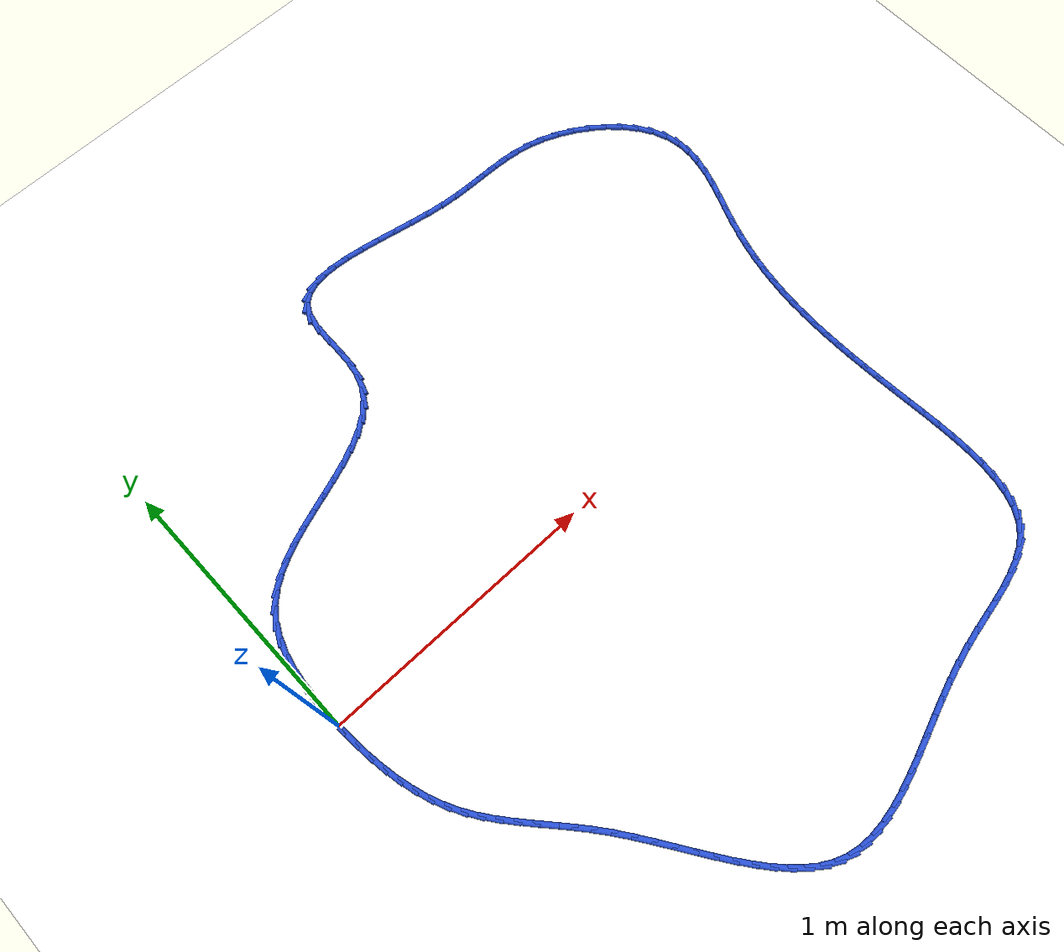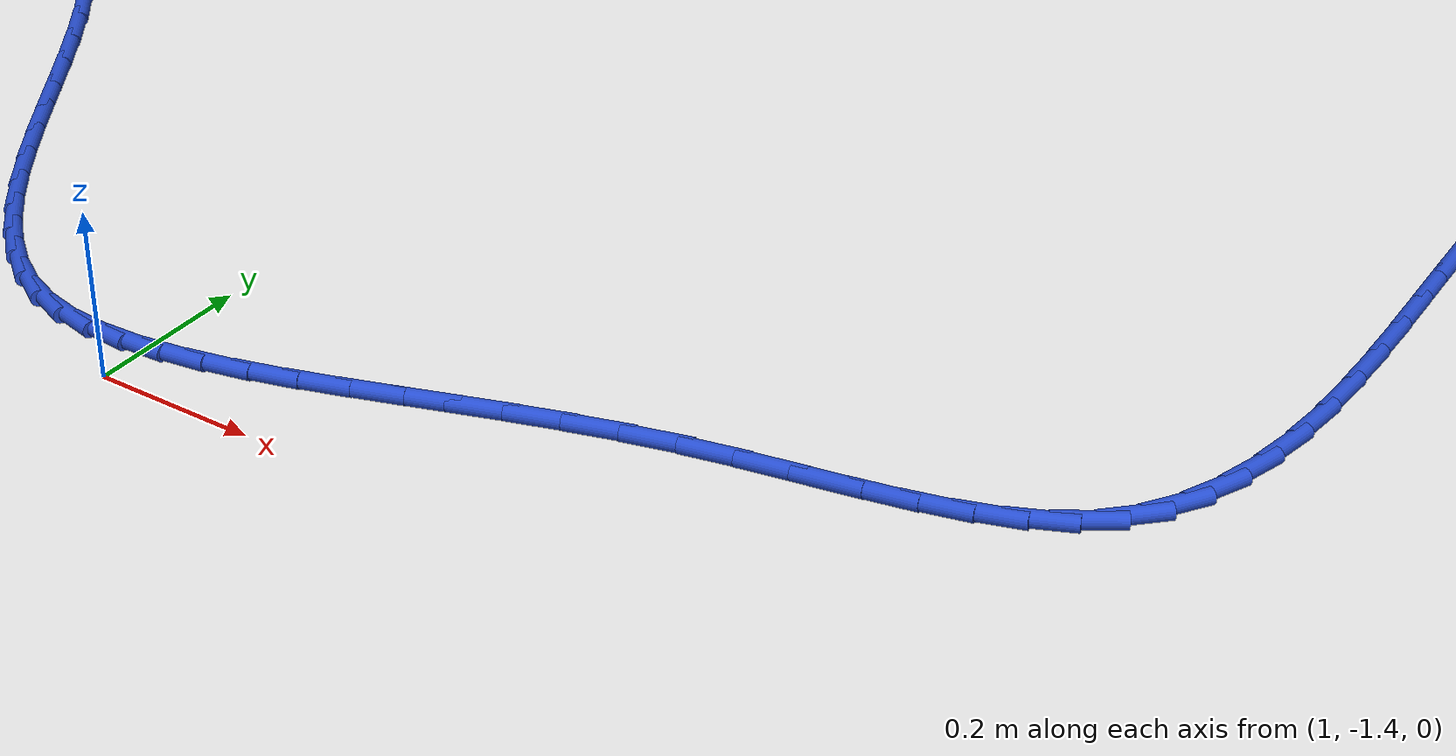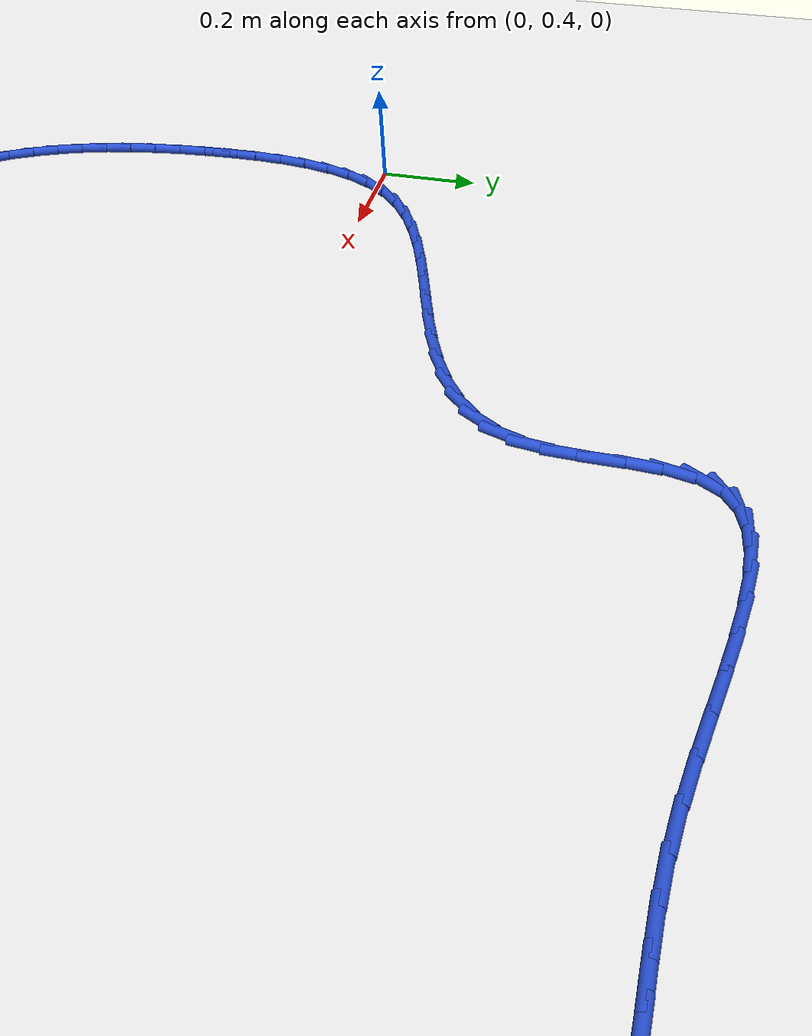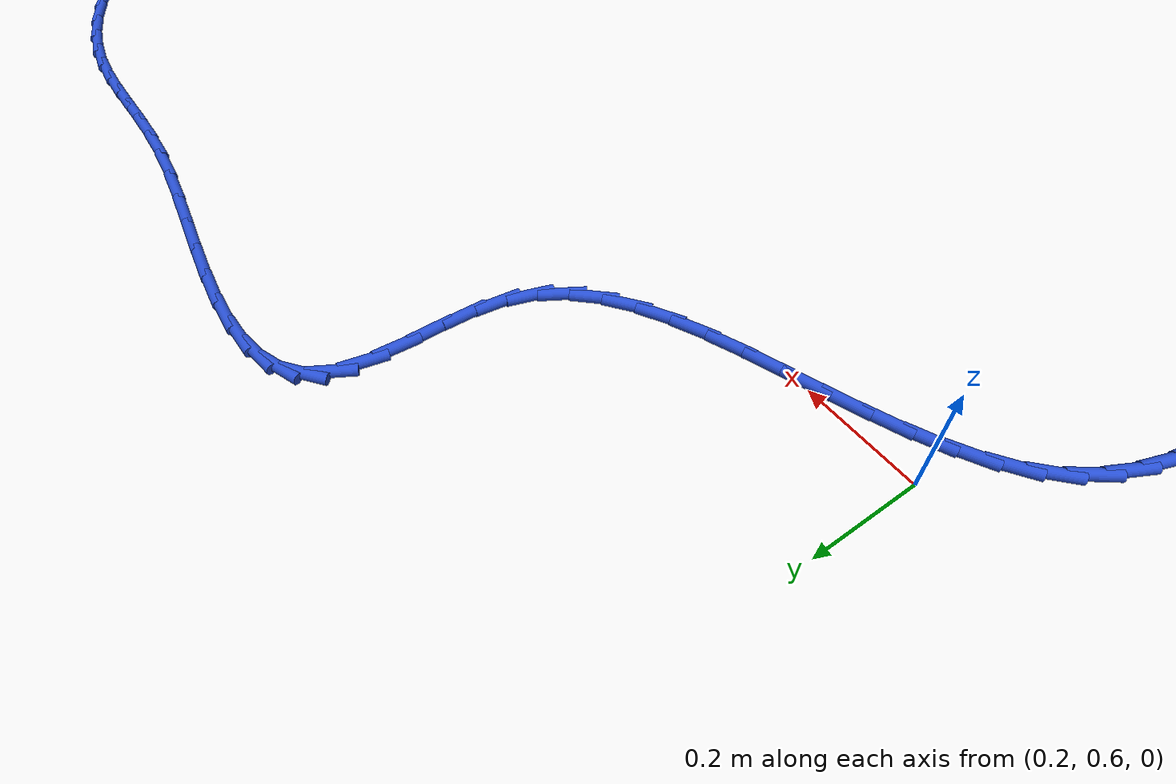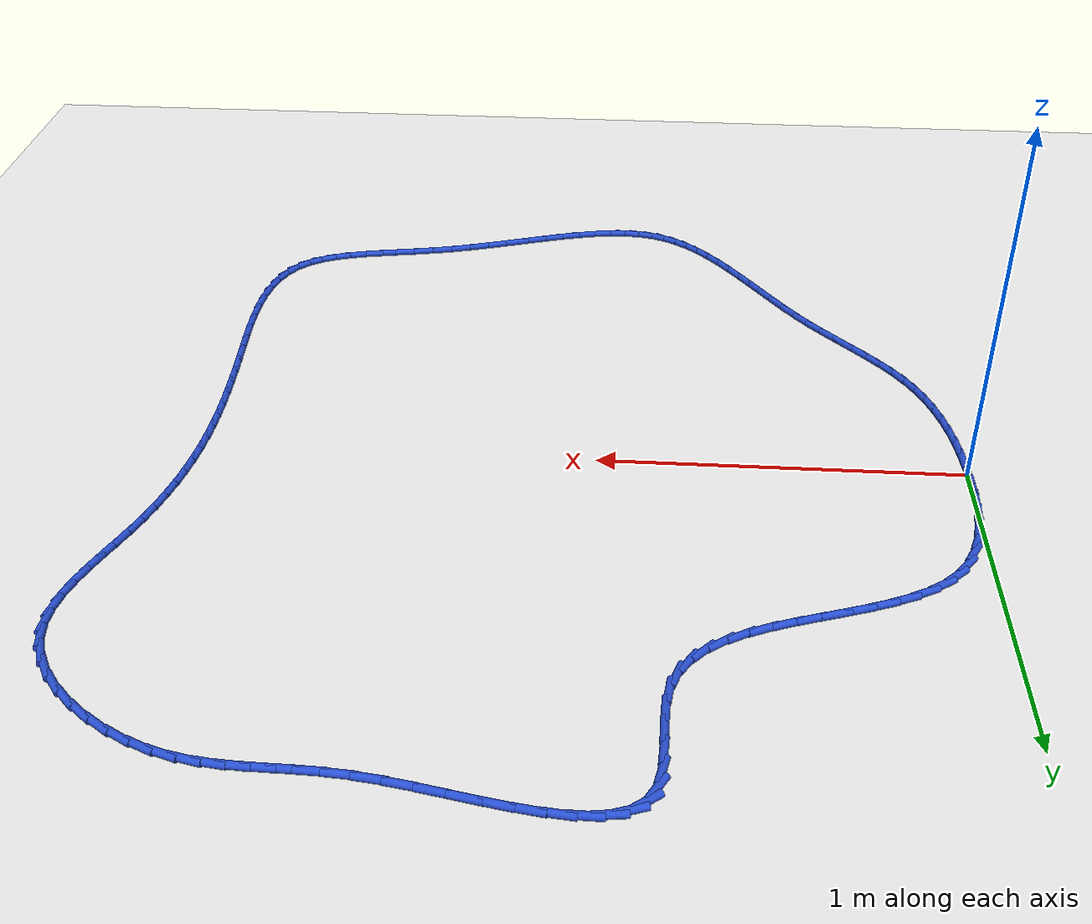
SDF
<sdf version="1.6">
 <world name="default">
  <light name="sun" type="directional">
   <pose>0 0 10 0 -0 0</pose>
   <diffuse>0.8 0.8 0.8 1</diffuse>
   <specular>0.2 0.2 0.2 1</specular>
   <attenuation>
    <range>1000</range>
    <constant>0.9</constant>
    <linear>0.01</linear>
    <quadratic>0.001</quadratic>
   </attenuation>
   <direction>-0.5 0.1 -0.9</direction>
  </light>
  <model name="ground_plane">
   <static>1</static>
   <link name="link">
    <collision name="collision">
     <geometry><plane><normal>0 0 1</normal><size>100 100</size></plane></geometry>
     <surface><friction><ode><mu>100</mu><mu2>50</mu2></ode></friction></surface>
    </collision>
    <visual name="visual">
     <cast_shadows>0</cast_shadows>
     <geometry><plane><normal>0 0 1</normal><size>100 100</size></plane></geometry>
     <material>
      <script><uri>file://media/materials/scripts/gazebo.material</uri><name>Gazebo/WhiteGlow</name></script>
     </material>
    </visual>
   </link>
  </model>
  <gravity>0 0 -9.8</gravity>
  <magnetic_field>6e-06 2.3e-05 -4.2e-05</magnetic_field>
  <atmosphere type="adiabatic"/>
  <physics name="default_physics" default="0" type="ode">
   <max_step_size>0.001</max_step_size>
   <real_time_factor>1</real_time_factor>
   <real_time_update_rate>1000</real_time_update_rate>
  </physics>
  <scene><ambient>0.4 0.4 0.4 1</ambient><background>0.7 0.7 0.7 1</background><shadows>1</shadows></scene>
  <spherical_coordinates>
   <surface_model>EARTH_WGS84</surface_model>
   <latitude_deg>0</latitude_deg>
   <longitude_deg>0</longitude_deg>
   <elevation>0</elevation>
   <heading_deg>0</heading_deg>
  </spherical_coordinates>
  <model name="line">
   <link name="link_0">
    <pose>-1.0842021724855044e-17 -2.7755575615628914e-17 0.01 0 1.57 -1.546820665249024</pose>
    <collision name="collision">
     <geometry><cylinder><radius>0.01</radius><length>0.08</length></cylinder></geometry>
    </collision>
    <visual name="visual">
     <material>
      <script><name>Gazebo/Blue</name><uri>file://media/materials/scripts/gazebo.material</uri></script>
     </material>
     <geometry><cylinder><radius>0.01</radius><length>0.08</length></cylinder></geometry>
    </visual>
   </link>
   <link name="link_1">
    <pose>-0.0014482822844550166 0.0603947784526387 0.01 0 1.57 1.553900163379401</pose>
    <collision name="collision">
     <geometry><cylinder><radius>0.01</radius><length>0.08</length></cylinder></geometry>
    </collision>
    <visual name="visual">
     <material>
      <script><name>Gazebo/Blue</name><uri>file://media/materials/scripts/gazebo.material</uri></script>
     </material>
     <geometry><cylinder><radius>0.01</radius><length>0.08</length></cylinder></geometry>
    </visual>
   </link>
   <link name="link_2">
    <pose>-0.00042740290458333956 0.12080980912698046 0.01 0 1.57 1.4995469914829243</pose>
    <collision name="collision">
     <geometry><cylinder><radius>0.01</radius><length>0.08</length></cylinder></geometry>
    </collision>
    <visual name="visual">
     <material>
      <script><name>Gazebo/Blue</name><uri>file://media/materials/scripts/gazebo.material</uri></script>
     </material>
     <geometry><cylinder><radius>0.01</radius><length>0.08</length></cylinder></geometry>
    </visual>
   </link>
   <link name="link_3">
    <pose>0.003823991763133144 0.1803780590002816 0.01 0 1.57 1.4292661213409839</pose>
    <collision name="collision">
     <geometry><cylinder><radius>0.01</radius><length>0.08</length></cylinder></geometry>
    </collision>
    <visual name="visual">
     <material>
      <script><name>Gazebo/Blue</name><uri>file://media/materials/scripts/gazebo.material</uri></script>
     </material>
     <geometry><cylinder><radius>0.01</radius><length>0.08</length></cylinder></geometry>
    </visual>
   </link>
   <link name="link_4">
    <pose>0.012067255342212547 0.23823249504979815 0.01 0 1.57 1.3398610520253216</pose>
    <collision name="collision">
     <geometry><cylinder><radius>0.01</radius><length>0.08</length></cylinder></geometry>
    </collision>
    <visual name="visual">
     <material>
      <script><name>Gazebo/Blue</name><uri>file://media/materials/scripts/gazebo.material</uri></script>
     </material>
     <geometry><cylinder><radius>0.01</radius><length>0.08</length></cylinder></geometry>
    </visual>
   </link>
   <link name="link_5">
    <pose>0.025063741456173013 0.2935060842527867 0.01 0 1.57 1.2277402085793172</pose>
    <collision name="collision">
     <geometry><cylinder><radius>0.01</radius><length>0.08</length></cylinder></geometry>
    </collision>
    <visual name="visual">
     <material>
      <script><name>Gazebo/Blue</name><uri>file://media/materials/scripts/gazebo.material</uri></script>
     </material>
     <geometry><cylinder><radius>0.01</radius><length>0.08</length></cylinder></geometry>
    </visual>
   </link>
   <link name="link_6">
    <pose>0.04357480372853265 0.34533179358650323 0.01 0 1.57 1.089929720037065</pose>
    <collision name="collision">
     <geometry><cylinder><radius>0.01</radius><length>0.08</length></cylinder></geometry>
    </collision>
    <visual name="visual">
     <material>
      <script><name>Gazebo/Blue</name><uri>file://media/materials/scripts/gazebo.material</uri></script>
     </material>
     <geometry><cylinder><radius>0.01</radius><length>0.08</length></cylinder></geometry>
    </visual>
   </link>
   <link name="link_7">
    <pose>0.06836179578280957 0.3928425900282041 0.01 0 1.57 0.9261226858212825</pose>
    <collision name="collision">
     <geometry><cylinder><radius>0.01</radius><length>0.08</length></cylinder></geometry>
    </collision>
    <visual name="visual">
     <material>
      <script><name>Gazebo/Blue</name><uri>file://media/materials/scripts/gazebo.material</uri></script>
     </material>
     <geometry><cylinder><radius>0.01</radius><length>0.08</length></cylinder></geometry>
    </visual>
   </link>
   <link name="link_8">
    <pose>0.10018605969218394 0.43517145095094184 0.01 0 1.57 0.7505717292814116</pose>
    <collision name="collision">
     <geometry><cylinder><radius>0.01</radius><length>0.08</length></cylinder></geometry>
    </collision>
    <visual name="visual">
     <material>
      <script><name>Gazebo/Blue</name><uri>file://media/materials/scripts/gazebo.material</uri></script>
     </material>
     <geometry><cylinder><radius>0.01</radius><length>0.08</length></cylinder></geometry>
    </visual>
   </link>
   <link name="link_9">
    <pose>0.13944064829590896 0.47178282972128 0.01 0 1.57 0.6039710030051992</pose>
    <collision name="collision">
     <geometry><cylinder><radius>0.01</radius><length>0.08</length></cylinder></geometry>
    </collision>
    <visual name="visual">
     <material>
      <script><name>Gazebo/Blue</name><uri>file://media/materials/scripts/gazebo.material</uri></script>
     </material>
     <geometry><cylinder><radius>0.01</radius><length>0.08</length></cylinder></geometry>
    </visual>
   </link>
   <link name="link_10">
    <pose>0.185182399845223 0.5033438297354479 0.01 0 1.57 0.4939126290468347</pose>
    <collision name="collision">
     <geometry><cylinder><radius>0.01</radius><length>0.08</length></cylinder></geometry>
    </collision>
    <visual name="visual">
     <material>
      <script><name>Gazebo/Blue</name><uri>file://media/materials/scripts/gazebo.material</uri></script>
     </material>
     <geometry><cylinder><radius>0.01</radius><length>0.08</length></cylinder></geometry>
    </visual>
   </link>
   <link name="link_11">
    <pose>0.23616520550820141 0.5307942196650123 0.01 0 1.57 0.41586747498312904</pose>
    <collision name="collision">
     <geometry><cylinder><radius>0.01</radius><length>0.08</length></cylinder></geometry>
    </collision>
    <visual name="visual">
     <material>
      <script><name>Gazebo/Blue</name><uri>file://media/materials/scripts/gazebo.material</uri></script>
     </material>
     <geometry><cylinder><radius>0.01</radius><length>0.08</length></cylinder></geometry>
    </visual>
   </link>
   <link name="link_12">
    <pose>0.29114295645291965 0.5550737681815409 0.01 0 1.57 0.3648469183188532</pose>
    <collision name="collision">
     <geometry><cylinder><radius>0.01</radius><length>0.08</length></cylinder></geometry>
    </collision>
    <visual name="visual">
     <material>
      <script><name>Gazebo/Blue</name><uri>file://media/materials/scripts/gazebo.material</uri></script>
     </material>
     <geometry><cylinder><radius>0.01</radius><length>0.08</length></cylinder></geometry>
    </visual>
   </link>
   <link name="link_13">
    <pose>0.3488695438474534 0.5771222439566007 0.01 0 1.57 0.3370795373727516</pose>
    <collision name="collision">
     <geometry><cylinder><radius>0.01</radius><length>0.08</length></cylinder></geometry>
    </collision>
    <visual name="visual">
     <material>
      <script><name>Gazebo/Blue</name><uri>file://media/materials/scripts/gazebo.material</uri></script>
     </material>
     <geometry><cylinder><radius>0.01</radius><length>0.08</length></cylinder></geometry>
    </visual>
   </link>
   <link name="link_14">
    <pose>0.40809885885987773 0.5978794156617588 0.01 0 1.57 0.33045467531488554</pose>
    <collision name="collision">
     <geometry><cylinder><radius>0.01</radius><length>0.08</length></cylinder></geometry>
    </collision>
    <visual name="visual">
     <material>
      <script><name>Gazebo/Blue</name><uri>file://media/materials/scripts/gazebo.material</uri></script>
     </material>
     <geometry><cylinder><radius>0.01</radius><length>0.08</length></cylinder></geometry>
    </visual>
   </link>
   <link name="link_15">
    <pose>0.4675847926582685 0.6182850519685829 0.01 0 1.57 0.34457380934153925</pose>
    <collision name="collision">
     <geometry><cylinder><radius>0.01</radius><length>0.08</length></cylinder></geometry>
    </collision>
    <visual name="visual">
     <material>
      <script><name>Gazebo/Blue</name><uri>file://media/materials/scripts/gazebo.material</uri></script>
     </material>
     <geometry><cylinder><radius>0.01</radius><length>0.08</length></cylinder></geometry>
    </visual>
   </link>
   <link name="link_16">
    <pose>0.5260812364107011 0.6392789215486397 0.01 0 1.57 0.3807750102335403</pose>
    <collision name="collision">
     <geometry><cylinder><radius>0.01</radius><length>0.08</length></cylinder></geometry>
    </collision>
    <visual name="visual">
     <material>
      <script><name>Gazebo/Blue</name><uri>file://media/materials/scripts/gazebo.material</uri></script>
     </material>
     <geometry><cylinder><radius>0.01</radius><length>0.08</length></cylinder></geometry>
    </visual>
   </link>
   <link name="link_17">
    <pose>0.582342081285251 0.661800793073497 0.01 0 1.57 0.44220395985941413</pose>
    <collision name="collision">
     <geometry><cylinder><radius>0.01</radius><length>0.08</length></cylinder></geometry>
    </collision>
    <visual name="visual">
     <material>
      <script><name>Gazebo/Blue</name><uri>file://media/materials/scripts/gazebo.material</uri></script>
     </material>
     <geometry><cylinder><radius>0.01</radius><length>0.08</length></cylinder></geometry>
    </visual>
   </link>
   <link name="link_18">
    <pose>0.6351212184499933 0.6867904352147214 0.01 0 1.57 0.5337578471949486</pose>
    <collision name="collision">
     <geometry><cylinder><radius>0.01</radius><length>0.08</length></cylinder></geometry>
    </collision>
    <visual name="visual">
     <material>
      <script><name>Gazebo/Blue</name><uri>file://media/materials/scripts/gazebo.material</uri></script>
     </material>
     <geometry><cylinder><radius>0.01</radius><length>0.08</length></cylinder></geometry>
    </visual>
   </link>
   <link name="link_19">
    <pose>0.6831725390730041 0.7151876166438806 0.01 0 1.57 0.6613041256950026</pose>
    <collision name="collision">
     <geometry><cylinder><radius>0.01</radius><length>0.08</length></cylinder></geometry>
    </collision>
    <visual name="visual">
     <material>
      <script><name>Gazebo/Blue</name><uri>file://media/materials/scripts/gazebo.material</uri></script>
     </material>
     <geometry><cylinder><radius>0.01</radius><length>0.08</length></cylinder></geometry>
    </visual>
   </link>
   <link name="link_20">
    <pose>0.7252499343223586 0.7479321060325419 0.01 0 1.57 0.8289191862085481</pose>
    <collision name="collision">
     <geometry><cylinder><radius>0.01</radius><length>0.08</length></cylinder></geometry>
    </collision>
    <visual name="visual">
     <material>
      <script><name>Gazebo/Blue</name><uri>file://media/materials/scripts/gazebo.material</uri></script>
     </material>
     <geometry><cylinder><radius>0.01</radius><length>0.08</length></cylinder></geometry>
    </visual>
   </link>
   <link name="link_21">
    <pose>0.7601072953661319 0.7859636720522722 0.01 0 1.57 1.0331030674142934</pose>
    <collision name="collision">
     <geometry><cylinder><radius>0.01</radius><length>0.08</length></cylinder></geometry>
    </collision>
    <visual name="visual">
     <material>
      <script><name>Gazebo/Blue</name><uri>file://media/materials/scripts/gazebo.material</uri></script>
     </material>
     <geometry><cylinder><radius>0.01</radius><length>0.08</length></cylinder></geometry>
    </visual>
   </link>
   <link name="link_22">
    <pose>0.7864985133724005 0.8302220833746394 0.01 0 1.57 1.2564844759627043</pose>
    <collision name="collision">
     <geometry><cylinder><radius>0.01</radius><length>0.08</length></cylinder></geometry>
    </collision>
    <visual name="visual">
     <material>
      <script><name>Gazebo/Blue</name><uri>file://media/materials/scripts/gazebo.material</uri></script>
     </material>
     <geometry><cylinder><radius>0.01</radius><length>0.08</length></cylinder></geometry>
    </visual>
   </link>
   <link name="link_23">
    <pose>0.8032076199773127 0.881620738814093 0.01 0 1.57 1.4379182021878878</pose>
    <collision name="collision">
     <geometry><cylinder><radius>0.01</radius><length>0.08</length></cylinder></geometry>
    </collision>
    <visual name="visual">
     <material>
      <script><name>Gazebo/Blue</name><uri>file://media/materials/scripts/gazebo.material</uri></script>
     </material>
     <geometry><cylinder><radius>0.01</radius><length>0.08</length></cylinder></geometry>
    </visual>
   </link>
   <link name="link_24">
    <pose>0.8109307471581267 0.939400143032776 0.01 0 1.57 1.5303563521007466</pose>
    <collision name="collision">
     <geometry><cylinder><radius>0.01</radius><length>0.08</length></cylinder></geometry>
    </collision>
    <visual name="visual">
     <material>
      <script><name>Gazebo/Blue</name><uri>file://media/materials/scripts/gazebo.material</uri></script>
     </material>
     <geometry><cylinder><radius>0.01</radius><length>0.08</length></cylinder></geometry>
    </visual>
   </link>
   <link name="link_25">
    <pose>0.8133889827476557 1.000154270668778 0.01 0 1.57 1.5511291409833468</pose>
    <collision name="collision">
     <geometry><cylinder><radius>0.01</radius><length>0.08</length></cylinder></geometry>
    </collision>
    <visual name="visual">
     <material>
      <script><name>Gazebo/Blue</name><uri>file://media/materials/scripts/gazebo.material</uri></script>
     </material>
     <geometry><cylinder><radius>0.01</radius><length>0.08</length></cylinder></geometry>
    </visual>
   </link>
   <link name="link_26">
    <pose>0.8145709125791069 1.0602430627004527 0.01 0 1.57 1.5010999197297845</pose>
    <collision name="collision">
     <geometry><cylinder><radius>0.01</radius><length>0.08</length></cylinder></geometry>
    </collision>
    <visual name="visual">
     <material>
      <script><name>Gazebo/Blue</name><uri>file://media/materials/scripts/gazebo.material</uri></script>
     </material>
     <geometry><cylinder><radius>0.01</radius><length>0.08</length></cylinder></geometry>
    </visual>
   </link>
   <link name="link_27">
    <pose>0.8184651224856869 1.1160264601061534 0.01 0 1.57 1.3528362201876207</pose>
    <collision name="collision">
     <geometry><cylinder><radius>0.01</radius><length>0.08</length></cylinder></geometry>
    </collision>
    <visual name="visual">
     <material>
      <script><name>Gazebo/Blue</name><uri>file://media/materials/scripts/gazebo.material</uri></script>
     </material>
     <geometry><cylinder><radius>0.01</radius><length>0.08</length></cylinder></geometry>
    </visual>
   </link>
   <link name="link_28">
    <pose>0.8290601983006023 1.1638644038642334 0.01 0 1.57 1.050256642923014</pose>
    <collision name="collision">
     <geometry><cylinder><radius>0.01</radius><length>0.08</length></cylinder></geometry>
    </collision>
    <visual name="visual">
     <material>
      <script><name>Gazebo/Blue</name><uri>file://media/materials/scripts/gazebo.material</uri></script>
     </material>
     <geometry><cylinder><radius>0.01</radius><length>0.08</length></cylinder></geometry>
    </visual>
   </link>
   <link name="link_29">
    <pose>0.8500208368602044 1.2004271438908194 0.01 0 1.57 0.6669584662122099</pose>
    <collision name="collision">
     <geometry><cylinder><radius>0.01</radius><length>0.08</length></cylinder></geometry>
    </collision>
    <visual name="visual">
     <material>
      <script><name>Gazebo/Blue</name><uri>file://media/materials/scripts/gazebo.material</uri></script>
     </material>
     <geometry><cylinder><radius>0.01</radius><length>0.08</length></cylinder></geometry>
    </visual>
   </link>
   <link name="link_30">
    <pose>0.8818083837141905 1.2254539708682435 0.01 0 1.57 0.34838797273996663</pose>
    <collision name="collision">
     <geometry><cylinder><radius>0.01</radius><length>0.08</length></cylinder></geometry>
    </collision>
    <visual name="visual">
     <material>
      <script><name>Gazebo/Blue</name><uri>file://media/materials/scripts/gazebo.material</uri></script>
     </material>
     <geometry><cylinder><radius>0.01</radius><length>0.08</length></cylinder></geometry>
    </visual>
   </link>
   <link name="link_31">
    <pose>0.9230563702762906 1.2404353527910792 0.01 0 1.57 0.12997595618460264</pose>
    <collision name="collision">
     <geometry><cylinder><radius>0.01</radius><length>0.08</length></cylinder></geometry>
    </collision>
    <visual name="visual">
     <material>
      <script><name>Gazebo/Blue</name><uri>file://media/materials/scripts/gazebo.material</uri></script>
     </material>
     <geometry><cylinder><radius>0.01</radius><length>0.08</length></cylinder></geometry>
    </visual>
   </link>
   <link name="link_32">
    <pose>0.9723769980258046 1.2468821932641252 0.01 0 1.57 -0.010298582900003274</pose>
    <collision name="collision">
     <geometry><cylinder><radius>0.01</radius><length>0.08</length></cylinder></geometry>
    </collision>
    <visual name="visual">
     <material>
      <script><name>Gazebo/Blue</name><uri>file://media/materials/scripts/gazebo.material</uri></script>
     </material>
     <geometry><cylinder><radius>0.01</radius><length>0.08</length></cylinder></geometry>
    </visual>
   </link>
   <link name="link_33">
    <pose>1.0283824684420317 1.2463053958921804 0.01 0 1.57 -0.09901094173558654</pose>
    <collision name="collision">
     <geometry><cylinder><radius>0.01</radius><length>0.08</length></cylinder></geometry>
    </collision>
    <visual name="visual">
     <material>
      <script><name>Gazebo/Blue</name><uri>file://media/materials/scripts/gazebo.material</uri></script>
     </material>
     <geometry><cylinder><radius>0.01</radius><length>0.08</length></cylinder></geometry>
    </visual>
   </link>
   <link name="link_34">
    <pose>1.0896849830042714 1.2402158642800432 0.01 0 1.57 -0.15352979537831013</pose>
    <collision name="collision">
     <geometry><cylinder><radius>0.01</radius><length>0.08</length></cylinder></geometry>
    </collision>
    <visual name="visual">
     <material>
      <script><name>Gazebo/Blue</name><uri>file://media/materials/scripts/gazebo.material</uri></script>
     </material>
     <geometry><cylinder><radius>0.01</radius><length>0.08</length></cylinder></geometry>
    </visual>
   </link>
   <link name="link_35">
    <pose>1.1548967431918238 1.2301245020325131 0.01 0 1.57 -0.18366892343678137</pose>
    <collision name="collision">
     <geometry><cylinder><radius>0.01</radius><length>0.08</length></cylinder></geometry>
    </collision>
    <visual name="visual">
     <material>
      <script><name>Gazebo/Blue</name><uri>file://media/materials/scripts/gazebo.material</uri></script>
     </material>
     <geometry><cylinder><radius>0.01</radius><length>0.08</length></cylinder></geometry>
    </visual>
   </link>
   <link name="link_36">
    <pose>1.2226299504839877 1.2175422127543887 0.01 0 1.57 -0.19444697268387648</pose>
    <collision name="collision">
     <geometry><cylinder><radius>0.01</radius><length>0.08</length></cylinder></geometry>
    </collision>
    <visual name="visual">
     <material>
      <script><name>Gazebo/Blue</name><uri>file://media/materials/scripts/gazebo.material</uri></script>
     </material>
     <geometry><cylinder><radius>0.01</radius><length>0.08</length></cylinder></geometry>
    </visual>
   </link>
   <link name="link_37">
    <pose>1.2914968063600636 1.2039799000504683 0.01 0 1.57 -0.1876918706073959</pose>
    <collision name="collision">
     <geometry><cylinder><radius>0.01</radius><length>0.08</length></cylinder></geometry>
    </collision>
    <visual name="visual">
     <material>
      <script><name>Gazebo/Blue</name><uri>file://media/materials/scripts/gazebo.material</uri></script>
     </material>
     <geometry><cylinder><radius>0.01</radius><length>0.08</length></cylinder></geometry>
    </visual>
   </link>
   <link name="link_38">
    <pose>1.3601095122993505 1.1909484675255515 0.01 0 1.57 -0.16264667313331255</pose>
    <collision name="collision">
     <geometry><cylinder><radius>0.01</radius><length>0.08</length></cylinder></geometry>
    </collision>
    <visual name="visual">
     <material>
      <script><name>Gazebo/Blue</name><uri>file://media/materials/scripts/gazebo.material</uri></script>
     </material>
     <geometry><cylinder><radius>0.01</radius><length>0.08</length></cylinder></geometry>
    </visual>
   </link>
   <link name="link_39">
    <pose>1.427080269781148 1.1799588187844368 0.01 0 1.57 -0.1162900253006017</pose>
    <collision name="collision">
     <geometry><cylinder><radius>0.01</radius><length>0.08</length></cylinder></geometry>
    </collision>
    <visual name="visual">
     <material>
      <script><name>Gazebo/Blue</name><uri>file://media/materials/scripts/gazebo.material</uri></script>
     </material>
     <geometry><cylinder><radius>0.01</radius><length>0.08</length></cylinder></geometry>
    </visual>
   </link>
   <link name="link_40">
    <pose>1.491045710836937 1.1724865622558065 0.01 0 1.57 -0.06189265783912024</pose>
    <collision name="collision">
     <geometry><cylinder><radius>0.01</radius><length>0.08</length></cylinder></geometry>
    </collision>
    <visual name="visual">
     <material>
      <script><name>Gazebo/Blue</name><uri>file://media/materials/scripts/gazebo.material</uri></script>
     </material>
     <geometry><cylinder><radius>0.01</radius><length>0.08</length></cylinder></geometry>
    </visual>
   </link>
   <link name="link_41">
    <pose>1.5515204781953047 1.1687388314704257 0.01 0 1.57 -0.024410377347635116</pose>
    <collision name="collision">
     <geometry><cylinder><radius>0.01</radius><length>0.08</length></cylinder></geometry>
    </collision>
    <visual name="visual">
     <material>
      <script><name>Gazebo/Blue</name><uri>file://media/materials/scripts/gazebo.material</uri></script>
     </material>
     <geometry><cylinder><radius>0.01</radius><length>0.08</length></cylinder></geometry>
    </visual>
   </link>
   <link name="link_42">
    <pose>1.6091199388111672 1.167332527567537 0.01 0 1.57 -0.009901554772065769</pose>
    <collision name="collision">
     <geometry><cylinder><radius>0.01</radius><length>0.08</length></cylinder></geometry>
    </collision>
    <visual name="visual">
     <material>
      <script><name>Gazebo/Blue</name><uri>file://media/materials/scripts/gazebo.material</uri></script>
     </material>
     <geometry><cylinder><radius>0.01</radius><length>0.08</length></cylinder></geometry>
    </visual>
   </link>
   <link name="link_43">
    <pose>1.6645291477037238 1.166783872320496 0.01 0 1.57 -0.0217905648158715</pose>
    <collision name="collision">
     <geometry><cylinder><radius>0.01</radius><length>0.08</length></cylinder></geometry>
    </collision>
    <visual name="visual">
     <material>
      <script><name>Gazebo/Blue</name><uri>file://media/materials/scripts/gazebo.material</uri></script>
     </material>
     <geometry><cylinder><radius>0.01</radius><length>0.08</length></cylinder></geometry>
    </visual>
   </link>
   <link name="link_44">
    <pose>1.7184331598921756 1.16560908750266 0.01 0 1.57 -0.061798622239073224</pose>
    <collision name="collision">
     <geometry><cylinder><radius>0.01</radius><length>0.08</length></cylinder></geometry>
    </collision>
    <visual name="visual">
     <material>
      <script><name>Gazebo/Blue</name><uri>file://media/materials/scripts/gazebo.material</uri></script>
     </material>
     <geometry><cylinder><radius>0.01</radius><length>0.08</length></cylinder></geometry>
    </visual>
   </link>
   <link name="link_45">
    <pose>1.7715170303957202 1.162324394887384 0.01 0 1.57 -0.12918282378274612</pose>
    <collision name="collision">
     <geometry><cylinder><radius>0.01</radius><length>0.08</length></cylinder></geometry>
    </collision>
    <visual name="visual">
     <material>
      <script><name>Gazebo/Blue</name><uri>file://media/materials/scripts/gazebo.material</uri></script>
     </material>
     <geometry><cylinder><radius>0.01</radius><length>0.08</length></cylinder></geometry>
    </visual>
   </link>
   <link name="link_46">
    <pose>1.824465814233559 1.1554460162480256 0.01 0 1.57 -0.2198661773612178</pose>
    <collision name="collision">
     <geometry><cylinder><radius>0.01</radius><length>0.08</length></cylinder></geometry>
    </collision>
    <visual name="visual">
     <material>
      <script><name>Gazebo/Blue</name><uri>file://media/materials/scripts/gazebo.material</uri></script>
     </material>
     <geometry><cylinder><radius>0.01</radius><length>0.08</length></cylinder></geometry>
    </visual>
   </link>
   <link name="link_47">
    <pose>1.8779645664248898 1.1434901733579397 0.01 0 1.57 -0.3228208349715841</pose>
    <collision name="collision">
     <geometry><cylinder><radius>0.01</radius><length>0.08</length></cylinder></geometry>
    </collision>
    <visual name="visual">
     <material>
      <script><name>Gazebo/Blue</name><uri>file://media/materials/scripts/gazebo.material</uri></script>
     </material>
     <geometry><cylinder><radius>0.01</radius><length>0.08</length></cylinder></geometry>
    </visual>
   </link>
   <link name="link_48">
    <pose>1.932406903756399 1.1252779615877784 0.01 0 1.57 -0.41926896428312277</pose>
    <collision name="collision">
     <geometry><cylinder><radius>0.01</radius><length>0.08</length></cylinder></geometry>
    </collision>
    <visual name="visual">
     <material>
      <script><name>Gazebo/Blue</name><uri>file://media/materials/scripts/gazebo.material</uri></script>
     </material>
     <geometry><cylinder><radius>0.01</radius><length>0.08</length></cylinder></geometry>
    </visual>
   </link>
   <link name="link_49">
    <pose>1.9868760469823592 1.1010012818776396 0.01 0 1.57 -0.5100011967996134</pose>
    <collision name="collision">
     <geometry><cylinder><radius>0.01</radius><length>0.08</length></cylinder></geometry>
    </collision>
    <visual name="visual">
     <material>
      <script><name>Gazebo/Blue</name><uri>file://media/materials/scripts/gazebo.material</uri></script>
     </material>
     <geometry><cylinder><radius>0.01</radius><length>0.08</length></cylinder></geometry>
    </visual>
   </link>
   <link name="link_50">
    <pose>2.040087080061496 1.0712371431480954 0.01 0 1.57 -0.6001442837054394</pose>
    <collision name="collision">
     <geometry><cylinder><radius>0.01</radius><length>0.08</length></cylinder></geometry>
    </collision>
    <visual name="visual">
     <material>
      <script><name>Gazebo/Blue</name><uri>file://media/materials/scripts/gazebo.material</uri></script>
     </material>
     <geometry><cylinder><radius>0.01</radius><length>0.08</length></cylinder></geometry>
    </visual>
   </link>
   <link name="link_51">
    <pose>2.090755067546293 1.0365625746205862 0.01 0 1.57 -0.6944185450121094</pose>
    <collision name="collision">
     <geometry><cylinder><radius>0.01</radius><length>0.08</length></cylinder></geometry>
    </collision>
    <visual name="visual">
     <material>
      <script><name>Gazebo/Blue</name><uri>file://media/materials/scripts/gazebo.material</uri></script>
     </material>
     <geometry><cylinder><radius>0.01</radius><length>0.08</length></cylinder></geometry>
    </visual>
   </link>
   <link name="link_52">
    <pose>2.1375950739892375 0.997554605516552 0.01 0 1.57 -0.7976739456535579</pose>
    <collision name="collision">
     <geometry><cylinder><radius>0.01</radius><length>0.08</length></cylinder></geometry>
    </collision>
    <visual name="visual">
     <material>
      <script><name>Gazebo/Blue</name><uri>file://media/materials/scripts/gazebo.material</uri></script>
     </material>
     <geometry><cylinder><radius>0.01</radius><length>0.08</length></cylinder></geometry>
    </visual>
   </link>
   <link name="link_53">
    <pose>2.179322163942816 0.9547902650574335 0.01 0 1.57 -0.9152655840612712</pose>
    <collision name="collision">
     <geometry><cylinder><radius>0.01</radius><length>0.08</length></cylinder></geometry>
    </collision>
    <visual name="visual">
     <material>
      <script><name>Gazebo/Blue</name><uri>file://media/materials/scripts/gazebo.material</uri></script>
     </material>
     <geometry><cylinder><radius>0.01</radius><length>0.08</length></cylinder></geometry>
    </visual>
   </link>
   <link name="link_54">
    <pose>2.214651401959514 0.9088465824646703 0.01 0 1.57 -1.0531129473549132</pose>
    <collision name="collision">
     <geometry><cylinder><radius>0.01</radius><length>0.08</length></cylinder></geometry>
    </collision>
    <visual name="visual">
     <material>
      <script><name>Gazebo/Blue</name><uri>file://media/materials/scripts/gazebo.material</uri></script>
     </material>
     <geometry><cylinder><radius>0.01</radius><length>0.08</length></cylinder></geometry>
    </visual>
   </link>
   <link name="link_55">
    <pose>2.2422978525918174 0.8603005869597031 0.01 0 1.57 -1.2169843292213263</pose>
    <collision name="collision">
     <geometry><cylinder><radius>0.01</radius><length>0.08</length></cylinder></geometry>
    </collision>
    <visual name="visual">
     <material>
      <script><name>Gazebo/Blue</name><uri>file://media/materials/scripts/gazebo.material</uri></script>
     </material>
     <geometry><cylinder><radius>0.01</radius><length>0.08</length></cylinder></geometry>
    </visual>
   </link>
   <link name="link_56">
    <pose>2.260976580392213 0.8097293077639723 0.01 0 1.57 -1.408436548187252</pose>
    <collision name="collision">
     <geometry><cylinder><radius>0.01</radius><length>0.08</length></cylinder></geometry>
    </collision>
    <visual name="visual">
     <material>
      <script><name>Gazebo/Blue</name><uri>file://media/materials/scripts/gazebo.material</uri></script>
     </material>
     <geometry><cylinder><radius>0.01</radius><length>0.08</length></cylinder></geometry>
    </visual>
   </link>
   <link name="link_57">
    <pose>2.2694991461197414 0.7576995074178495 0.01 0 1.57 1.5486401529036067</pose>
    <collision name="collision">
     <geometry><cylinder><radius>0.01</radius><length>0.08</length></cylinder></geometry>
    </collision>
    <visual name="visual">
     <material>
      <script><name>Gazebo/Blue</name><uri>file://media/materials/scripts/gazebo.material</uri></script>
     </material>
     <geometry><cylinder><radius>0.01</radius><length>0.08</length></cylinder></geometry>
    </visual>
   </link>
   <link name="link_58">
    <pose>2.2683225355613668 0.7046028840256333 0.01 0 1.57 1.4046726871704147</pose>
    <collision name="collision">
     <geometry><cylinder><radius>0.01</radius><length>0.08</length></cylinder></geometry>
    </collision>
    <visual name="visual">
     <material>
      <script><name>Gazebo/Blue</name><uri>file://media/materials/scripts/gazebo.material</uri></script>
     </material>
     <geometry><cylinder><radius>0.01</radius><length>0.08</length></cylinder></geometry>
    </visual>
   </link>
   <link name="link_59">
    <pose>2.2592820983150124 0.6506844851428729 0.01 0 1.57 1.3017657845554083</pose>
    <collision name="collision">
     <geometry><cylinder><radius>0.01</radius><length>0.08</length></cylinder></geometry>
    </collision>
    <visual name="visual">
     <material>
      <script><name>Gazebo/Blue</name><uri>file://media/materials/scripts/gazebo.material</uri></script>
     </material>
     <geometry><cylinder><radius>0.01</radius><length>0.08</length></cylinder></geometry>
    </visual>
   </link>
   <link name="link_60">
    <pose>2.2442557422322778 0.5961848303541974 0.01 0 1.57 1.2350927831389917</pose>
    <collision name="collision">
     <geometry><cylinder><radius>0.01</radius><length>0.08</length></cylinder></geometry>
    </collision>
    <visual name="visual">
     <material>
      <script><name>Gazebo/Blue</name><uri>file://media/materials/scripts/gazebo.material</uri></script>
     </material>
     <geometry><cylinder><radius>0.01</radius><length>0.08</length></cylinder></geometry>
    </visual>
   </link>
   <link name="link_61">
    <pose>2.2251213751647647 0.5413444392442341 0.01 0 1.57 1.199925935378097</pose>
    <collision name="collision">
     <geometry><cylinder><radius>0.01</radius><length>0.08</length></cylinder></geometry>
    </collision>
    <visual name="visual">
     <material>
      <script><name>Gazebo/Blue</name><uri>file://media/materials/scripts/gazebo.material</uri></script>
     </material>
     <geometry><cylinder><radius>0.01</radius><length>0.08</length></cylinder></geometry>
    </visual>
   </link>
   <link name="link_62">
    <pose>2.203756904964073 0.4864038313976119 0.01 0 1.57 1.1934946358861824</pose>
    <collision name="collision">
     <geometry><cylinder><radius>0.01</radius><length>0.08</length></cylinder></geometry>
    </collision>
    <visual name="visual">
     <material>
      <script><name>Gazebo/Blue</name><uri>file://media/materials/scripts/gazebo.material</uri></script>
     </material>
     <geometry><cylinder><radius>0.01</radius><length>0.08</length></cylinder></geometry>
    </visual>
   </link>
   <link name="link_63">
    <pose>2.1820402394818013 0.4316035263989578 0.01 0 1.57 1.21532517691267</pose>
    <collision name="collision">
     <geometry><cylinder><radius>0.01</radius><length>0.08</length></cylinder></geometry>
    </collision>
    <visual name="visual">
     <material>
      <script><name>Gazebo/Blue</name><uri>file://media/materials/scripts/gazebo.material</uri></script>
     </material>
     <geometry><cylinder><radius>0.01</radius><length>0.08</length></cylinder></geometry>
    </visual>
   </link>
   <link name="link_64">
    <pose>2.1618366161466795 0.37718169070808305 0.01 0 1.57 1.2557580959203938</pose>
    <collision name="collision">
     <geometry><cylinder><radius>0.01</radius><length>0.08</length></cylinder></geometry>
    </collision>
    <visual name="visual">
     <material>
      <script><name>Gazebo/Blue</name><uri>file://media/materials/scripts/gazebo.material</uri></script>
     </material>
     <geometry><cylinder><radius>0.01</radius><length>0.08</length></cylinder></geometry>
    </visual>
   </link>
   <link name="link_65">
    <pose>2.144256249244159 0.32323626944296807 0.01 0 1.57 1.2976214716087273</pose>
    <collision name="collision">
     <geometry><cylinder><radius>0.01</radius><length>0.08</length></cylinder></geometry>
    </collision>
    <visual name="visual">
     <material>
      <script><name>Gazebo/Blue</name><uri>file://media/materials/scripts/gazebo.material</uri></script>
     </material>
     <geometry><cylinder><radius>0.01</radius><length>0.08</length></cylinder></geometry>
    </visual>
   </link>
   <link name="link_66">
    <pose>2.1292420487084387 0.26964841836366 0.01 0 1.57 1.3388521409441332</pose>
    <collision name="collision">
     <geometry><cylinder><radius>0.01</radius><length>0.08</length></cylinder></geometry>
    </collision>
    <visual name="visual">
     <material>
      <script><name>Gazebo/Blue</name><uri>file://media/materials/scripts/gazebo.material</uri></script>
     </material>
     <geometry><cylinder><radius>0.01</radius><length>0.08</length></cylinder></geometry>
    </visual>
   </link>
   <link name="link_67">
    <pose>2.116636858860883 0.21628070925085838 0.01 0 1.57 1.3788864061065833</pose>
    <collision name="collision">
     <geometry><cylinder><radius>0.01</radius><length>0.08</length></cylinder></geometry>
    </collision>
    <visual name="visual">
     <material>
      <script><name>Gazebo/Blue</name><uri>file://media/materials/scripts/gazebo.material</uri></script>
     </material>
     <geometry><cylinder><radius>0.01</radius><length>0.08</length></cylinder></geometry>
    </visual>
   </link>
   <link name="link_68">
    <pose>2.106283524022858 0.16299571388526096 0.01 0 1.57 1.417185159427692</pose>
    <collision name="collision">
     <geometry><cylinder><radius>0.01</radius><length>0.08</length></cylinder></geometry>
    </collision>
    <visual name="visual">
     <material>
      <script><name>Gazebo/Blue</name><uri>file://media/materials/scripts/gazebo.material</uri></script>
     </material>
     <geometry><cylinder><radius>0.01</radius><length>0.08</length></cylinder></geometry>
    </visual>
   </link>
   <link name="link_69">
    <pose>2.0980248885157278 0.10965600404756759 0.01 0 1.57 1.4532596387621757</pose>
    <collision name="collision">
     <geometry><cylinder><radius>0.01</radius><length>0.08</length></cylinder></geometry>
    </collision>
    <visual name="visual">
     <material>
      <script><name>Gazebo/Blue</name><uri>file://media/materials/scripts/gazebo.material</uri></script>
     </material>
     <geometry><cylinder><radius>0.01</radius><length>0.08</length></cylinder></geometry>
    </visual>
   </link>
   <link name="link_70">
    <pose>2.091703796660858 0.05612415151847604 0.01 0 1.57 1.486691745172485</pose>
    <collision name="collision">
     <geometry><cylinder><radius>0.01</radius><length>0.08</length></cylinder></geometry>
    </collision>
    <visual name="visual">
     <material>
      <script><name>Gazebo/Blue</name><uri>file://media/materials/scripts/gazebo.material</uri></script>
     </material>
     <geometry><cylinder><radius>0.01</radius><length>0.08</length></cylinder></geometry>
    </visual>
   </link>
   <link name="link_71">
    <pose>2.087163092779613 0.002262728078685952 0.01 0 1.57 1.517147207940919</pose>
    <collision name="collision">
     <geometry><cylinder><radius>0.01</radius><length>0.08</length></cylinder></geometry>
    </collision>
    <visual name="visual">
     <material>
      <script><name>Gazebo/Blue</name><uri>file://media/materials/scripts/gazebo.material</uri></script>
     </material>
     <geometry><cylinder><radius>0.01</radius><length>0.08</length></cylinder></geometry>
    </visual>
   </link>
   <link name="link_72">
    <pose>2.0842456211933587 -0.05206569449110433 0.01 0 1.57 1.5443812148516005</pose>
    <collision name="collision">
     <geometry><cylinder><radius>0.01</radius><length>0.08</length></cylinder></geometry>
    </collision>
    <visual name="visual">
     <material>
      <script><name>Gazebo/Blue</name><uri>file://media/materials/scripts/gazebo.material</uri></script>
     </material>
     <geometry><cylinder><radius>0.01</radius><length>0.08</length></cylinder></geometry>
    </visual>
   </link>
   <link name="link_73">
    <pose>2.0827942262234598 -0.10699854441019695 0.01 0 1.57 1.56823728818078</pose>
    <collision name="collision">
     <geometry><cylinder><radius>0.01</radius><length>0.08</length></cylinder></geometry>
    </collision>
    <visual name="visual">
     <material>
      <script><name>Gazebo/Blue</name><uri>file://media/materials/scripts/gazebo.material</uri></script>
     </material>
     <geometry><cylinder><radius>0.01</radius><length>0.08</length></cylinder></geometry>
    </visual>
   </link>
   <link name="link_74">
    <pose>2.0826517521912815 -0.1626732498978914 0.01 0 1.57 -1.5529517130383117</pose>
    <collision name="collision">
     <geometry><cylinder><radius>0.01</radius><length>0.08</length></cylinder></geometry>
    </collision>
    <visual name="visual">
     <material>
      <script><name>Gazebo/Blue</name><uri>file://media/materials/scripts/gazebo.material</uri></script>
     </material>
     <geometry><cylinder><radius>0.01</radius><length>0.08</length></cylinder></geometry>
    </visual>
   </link>
   <link name="link_75">
    <pose>2.083661043418189 -0.2192272391734897 0.01 0 1.57 -1.5360027241434457</pose>
    <collision name="collision">
     <geometry><cylinder><radius>0.01</radius><length>0.08</length></cylinder></geometry>
    </collision>
    <visual name="visual">
     <material>
      <script><name>Gazebo/Blue</name><uri>file://media/materials/scripts/gazebo.material</uri></script>
     </material>
     <geometry><cylinder><radius>0.01</radius><length>0.08</length></cylinder></geometry>
    </visual>
   </link>
   <link name="link_76">
    <pose>2.085664944225547 -0.27679794045629336 0.01 0 1.57 -1.522449826199268</pose>
    <collision name="collision">
     <geometry><cylinder><radius>0.01</radius><length>0.08</length></cylinder></geometry>
    </collision>
    <visual name="visual">
     <material>
      <script><name>Gazebo/Blue</name><uri>file://media/materials/scripts/gazebo.material</uri></script>
     </material>
     <geometry><cylinder><radius>0.01</radius><length>0.08</length></cylinder></geometry>
    </visual>
   </link>
   <link name="link_77">
    <pose>2.0885062989347207 -0.33552278196560326 0.01 0 1.57 -1.5121853663705571</pose>
    <collision name="collision">
     <geometry><cylinder><radius>0.01</radius><length>0.08</length></cylinder></geometry>
    </collision>
    <visual name="visual">
     <material>
      <script><name>Gazebo/Blue</name><uri>file://media/materials/scripts/gazebo.material</uri></script>
     </material>
     <geometry><cylinder><radius>0.01</radius><length>0.08</length></cylinder></geometry>
    </visual>
   </link>
   <link name="link_78">
    <pose>2.0920279518670757 -0.39553919192072196 0.01 0 1.57 -1.5050636957519175</pose>
    <collision name="collision">
     <geometry><cylinder><radius>0.01</radius><length>0.08</length></cylinder></geometry>
    </collision>
    <visual name="visual">
     <material>
      <script><name>Gazebo/Blue</name><uri>file://media/materials/scripts/gazebo.material</uri></script>
     </material>
     <geometry><cylinder><radius>0.01</radius><length>0.08</length></cylinder></geometry>
    </visual>
   </link>
   <link name="link_79">
    <pose>2.096072747343976 -0.45698459854094836 0.01 0 1.57 -1.501643881255641</pose>
    <collision name="collision">
     <geometry><cylinder><radius>0.01</radius><length>0.08</length></cylinder></geometry>
    </collision>
    <visual name="visual">
     <material>
      <script><name>Gazebo/Blue</name><uri>file://media/materials/scripts/gazebo.material</uri></script>
     </material>
     <geometry><cylinder><radius>0.01</radius><length>0.08</length></cylinder></geometry>
    </visual>
   </link>
   <link name="link_80">
    <pose>2.1004311447800097 -0.5199100354146243 0.01 0 1.57 -1.5069986258296735</pose>
    <collision name="collision">
     <geometry><cylinder><radius>0.01</radius><length>0.08</length></cylinder></geometry>
    </collision>
    <visual name="visual">
     <material>
      <script><name>Gazebo/Blue</name><uri>file://media/materials/scripts/gazebo.material</uri></script>
     </material>
     <geometry><cylinder><radius>0.01</radius><length>0.08</length></cylinder></geometry>
    </visual>
   </link>
   <link name="link_81">
    <pose>2.1045083155807567 -0.5837311085346446 0.01 0 1.57 -1.523389149344521</pose>
    <collision name="collision">
     <geometry><cylinder><radius>0.01</radius><length>0.08</length></cylinder></geometry>
    </collision>
    <visual name="visual">
     <material>
      <script><name>Gazebo/Blue</name><uri>file://media/materials/scripts/gazebo.material</uri></script>
     </material>
     <geometry><cylinder><radius>0.01</radius><length>0.08</length></cylinder></geometry>
    </visual>
   </link>
   <link name="link_82">
    <pose>2.1075374726445957 -0.6475798251880198 0.01 0 1.57 -1.5515379984079132</pose>
    <collision name="collision">
     <geometry><cylinder><radius>0.01</radius><length>0.08</length></cylinder></geometry>
    </collision>
    <visual name="visual">
     <material>
      <script><name>Gazebo/Blue</name><uri>file://media/materials/scripts/gazebo.material</uri></script>
     </material>
     <geometry><cylinder><radius>0.01</radius><length>0.08</length></cylinder></geometry>
    </visual>
   </link>
   <link name="link_83">
    <pose>2.108751033239691 -0.7105868804864948 0.01 0 1.57 1.548455737709211</pose>
    <collision name="collision">
     <geometry><cylinder><radius>0.01</radius><length>0.08</length></cylinder></geometry>
    </collision>
    <visual name="visual">
     <material>
      <script><name>Gazebo/Blue</name><uri>file://media/materials/scripts/gazebo.material</uri></script>
     </material>
     <geometry><cylinder><radius>0.01</radius><length>0.08</length></cylinder></geometry>
    </visual>
   </link>
   <link name="link_84">
    <pose>2.1073814146342054 -0.7718829695418168 0.01 0 1.57 1.490575179228844</pose>
    <collision name="collision">
     <geometry><cylinder><radius>0.01</radius><length>0.08</length></cylinder></geometry>
    </collision>
    <visual name="visual">
     <material>
      <script><name>Gazebo/Blue</name><uri>file://media/materials/scripts/gazebo.material</uri></script>
     </material>
     <geometry><cylinder><radius>0.01</radius><length>0.08</length></cylinder></geometry>
    </visual>
   </link>
   <link name="link_85">
    <pose>2.1026610340963017 -0.8305987874657319 0.01 0 1.57 1.41220940392731</pose>
    <collision name="collision">
     <geometry><cylinder><radius>0.01</radius><length>0.08</length></cylinder></geometry>
    </collision>
    <visual name="visual">
     <material>
      <script><name>Gazebo/Blue</name><uri>file://media/materials/scripts/gazebo.material</uri></script>
     </material>
     <geometry><cylinder><radius>0.01</radius><length>0.08</length></cylinder></geometry>
    </visual>
   </link>
   <link name="link_86">
    <pose>2.0938223088941457 -0.8858650293699866 0.01 0 1.57 1.307654174831309</pose>
    <collision name="collision">
     <geometry><cylinder><radius>0.01</radius><length>0.08</length></cylinder></geometry>
    </collision>
    <visual name="visual">
     <material>
      <script><name>Gazebo/Blue</name><uri>file://media/materials/scripts/gazebo.material</uri></script>
     </material>
     <geometry><cylinder><radius>0.01</radius><length>0.08</length></cylinder></geometry>
    </visual>
   </link>
   <link name="link_87">
    <pose>2.0800976562958993 -0.9368123903663279 0.01 0 1.57 1.170212591688762</pose>
    <collision name="collision">
     <geometry><cylinder><radius>0.01</radius><length>0.08</length></cylinder></geometry>
    </collision>
    <visual name="visual">
     <material>
      <script><name>Gazebo/Blue</name><uri>file://media/materials/scripts/gazebo.material</uri></script>
     </material>
     <geometry><cylinder><radius>0.01</radius><length>0.08</length></cylinder></geometry>
    </visual>
   </link>
   <link name="link_88">
    <pose>2.0607194935697266 -0.9825715655665006 0.01 0 1.57 0.9945422183669194</pose>
    <collision name="collision">
     <geometry><cylinder><radius>0.01</radius><length>0.08</length></cylinder></geometry>
    </collision>
    <visual name="visual">
     <material>
      <script><name>Gazebo/Blue</name><uri>file://media/materials/scripts/gazebo.material</uri></script>
     </material>
     <geometry><cylinder><radius>0.01</radius><length>0.08</length></cylinder></geometry>
    </visual>
   </link>
   <link name="link_89">
    <pose>2.034920237983791 -1.0222732500822518 0.01 0 1.57 0.7833570135102768</pose>
    <collision name="collision">
     <geometry><cylinder><radius>0.01</radius><length>0.08</length></cylinder></geometry>
    </collision>
    <visual name="visual">
     <material>
      <script><name>Gazebo/Blue</name><uri>file://media/materials/scripts/gazebo.material</uri></script>
     </material>
     <geometry><cylinder><radius>0.01</radius><length>0.08</length></cylinder></geometry>
    </visual>
   </link>
   <link name="link_90">
    <pose>2.001967922899663 -1.0550913177705665 0.01 0 1.57 0.5782835365766634</pose>
    <collision name="collision">
     <geometry><cylinder><radius>0.01</radius><length>0.08</length></cylinder></geometry>
    </collision>
    <visual name="visual">
     <material>
      <script><name>Gazebo/Blue</name><uri>file://media/materials/scripts/gazebo.material</uri></script>
     </material>
     <geometry><cylinder><radius>0.01</radius><length>0.08</length></cylinder></geometry>
    </visual>
   </link>
   <link name="link_91">
    <pose>1.9619600158048371 -1.0812051970394696 0.01 0 1.57 0.4200155871883968</pose>
    <collision name="collision">
     <geometry><cylinder><radius>0.01</radius><length>0.08</length></cylinder></geometry>
    </collision>
    <visual name="visual">
     <material>
      <script><name>Gazebo/Blue</name><uri>file://media/materials/scripts/gazebo.material</uri></script>
     </material>
     <geometry><cylinder><radius>0.01</radius><length>0.08</length></cylinder></geometry>
    </visual>
   </link>
   <link name="link_92">
    <pose>1.9158291609156402 -1.1018068328240305 0.01 0 1.57 0.30819702439163044</pose>
    <collision name="collision">
     <geometry><cylinder><radius>0.01</radius><length>0.08</length></cylinder></geometry>
    </collision>
    <visual name="visual">
     <material>
      <script><name>Gazebo/Blue</name><uri>file://media/materials/scripts/gazebo.material</uri></script>
     </material>
     <geometry><cylinder><radius>0.01</radius><length>0.08</length></cylinder></geometry>
    </visual>
   </link>
   <link name="link_93">
    <pose>1.8645447670795234 -1.11813274122054 0.01 0 1.57 0.23510601362853778</pose>
    <collision name="collision">
     <geometry><cylinder><radius>0.01</radius><length>0.08</length></cylinder></geometry>
    </collision>
    <visual name="visual">
     <material>
      <script><name>Gazebo/Blue</name><uri>file://media/materials/scripts/gazebo.material</uri></script>
     </material>
     <geometry><cylinder><radius>0.01</radius><length>0.08</length></cylinder></geometry>
    </visual>
   </link>
   <link name="link_94">
    <pose>1.8090762431439382 -1.1314194383252882 0.01 0 1.57 0.19325247205280616</pose>
    <collision name="collision">
     <geometry><cylinder><radius>0.01</radius><length>0.08</length></cylinder></geometry>
    </collision>
    <visual name="visual">
     <material>
      <script><name>Gazebo/Blue</name><uri>file://media/materials/scripts/gazebo.material</uri></script>
     </material>
     <geometry><cylinder><radius>0.01</radius><length>0.08</length></cylinder></geometry>
    </visual>
   </link>
   <link name="link_95">
    <pose>1.7503929979563357 -1.1429034402345657 0.01 0 1.57 0.1773087977708831</pose>
    <collision name="collision">
     <geometry><cylinder><radius>0.01</radius><length>0.08</length></cylinder></geometry>
    </collision>
    <visual name="visual">
     <material>
      <script><name>Gazebo/Blue</name><uri>file://media/materials/scripts/gazebo.material</uri></script>
     </material>
     <geometry><cylinder><radius>0.01</radius><length>0.08</length></cylinder></geometry>
    </visual>
   </link>
   <link name="link_96">
    <pose>1.6894644403641705 -1.153821263044662 0.01 0 1.57 0.18418019842987973</pose>
    <collision name="collision">
     <geometry><cylinder><radius>0.01</radius><length>0.08</length></cylinder></geometry>
    </collision>
    <visual name="visual">
     <material>
      <script><name>Gazebo/Blue</name><uri>file://media/materials/scripts/gazebo.material</uri></script>
     </material>
     <geometry><cylinder><radius>0.01</radius><length>0.08</length></cylinder></geometry>
    </visual>
   </link>
   <link name="link_97">
    <pose>1.6272599792148932 -1.1654094228518674 0.01 0 1.57 0.2126150158831517</pose>
    <collision name="collision">
     <geometry><cylinder><radius>0.01</radius><length>0.08</length></cylinder></geometry>
    </collision>
    <visual name="visual">
     <material>
      <script><name>Gazebo/Blue</name><uri>file://media/materials/scripts/gazebo.material</uri></script>
     </material>
     <geometry><cylinder><radius>0.01</radius><length>0.08</length></cylinder></geometry>
    </visual>
   </link>
   <link name="link_98">
    <pose>1.564748914829663 -1.1789041733128012 0.01 0 1.57 0.25542545267913946</pose>
    <collision name="collision">
     <geometry><cylinder><radius>0.01</radius><length>0.08</length></cylinder></geometry>
    </collision>
    <visual name="visual">
     <material>
      <script><name>Gazebo/Blue</name><uri>file://media/materials/scripts/gazebo.material</uri></script>
     </material>
     <geometry><cylinder><radius>0.01</radius><length>0.08</length></cylinder></geometry>
    </visual>
   </link>
   <link name="link_99">
    <pose>1.5027187189179012 -1.195102067805955 0.01 0 1.57 0.29093249980109287</pose>
    <collision name="collision">
     <geometry><cylinder><radius>0.01</radius><length>0.08</length></cylinder></geometry>
    </collision>
    <visual name="visual">
     <material>
      <script><name>Gazebo/Blue</name><uri>file://media/materials/scripts/gazebo.material</uri></script>
     </material>
     <geometry><cylinder><radius>0.01</radius><length>0.08</length></cylinder></geometry>
    </visual>
   </link>
   <link name="link_100">
    <pose>1.4414035326520016 -1.2134615887170255 0.01 0 1.57 0.3153230643764065</pose>
    <collision name="collision">
     <geometry><cylinder><radius>0.01</radius><length>0.08</length></cylinder></geometry>
    </collision>
    <visual name="visual">
     <material>
      <script><name>Gazebo/Blue</name><uri>file://media/materials/scripts/gazebo.material</uri></script>
     </material>
     <geometry><cylinder><radius>0.01</radius><length>0.08</length></cylinder></geometry>
    </visual>
   </link>
   <link name="link_101">
    <pose>1.3809326241909021 -1.2331876131671393 0.01 0 1.57 0.3287671724495455</pose>
    <collision name="collision">
     <geometry><cylinder><radius>0.01</radius><length>0.08</length></cylinder></geometry>
    </collision>
    <visual name="visual">
     <material>
      <script><name>Gazebo/Blue</name><uri>file://media/materials/scripts/gazebo.material</uri></script>
     </material>
     <geometry><cylinder><radius>0.01</radius><length>0.08</length></cylinder></geometry>
    </visual>
   </link>
   <link name="link_102">
    <pose>1.3214352616935374 -1.2534850182774253 0.01 0 1.57 0.3311042992151008</pose>
    <collision name="collision">
     <geometry><cylinder><radius>0.01</radius><length>0.08</length></cylinder></geometry>
    </collision>
    <visual name="visual">
     <material>
      <script><name>Gazebo/Blue</name><uri>file://media/materials/scripts/gazebo.material</uri></script>
     </material>
     <geometry><cylinder><radius>0.01</radius><length>0.08</length></cylinder></geometry>
    </visual>
   </link>
   <link name="link_103">
    <pose>1.2630407133188433 -1.2735586811690112 0.01 0 1.57 0.3217606691585787</pose>
    <collision name="collision">
     <geometry><cylinder><radius>0.01</radius><length>0.08</length></cylinder></geometry>
    </collision>
    <visual name="visual">
     <material>
      <script><name>Gazebo/Blue</name><uri>file://media/materials/scripts/gazebo.material</uri></script>
     </material>
     <geometry><cylinder><radius>0.01</radius><length>0.08</length></cylinder></geometry>
    </visual>
   </link>
   <link name="link_104">
    <pose>1.2058782472257545 -1.2926134789630248 0.01 0 1.57 0.2996647051833844</pose>
    <collision name="collision">
     <geometry><cylinder><radius>0.01</radius><length>0.08</length></cylinder></geometry>
    </collision>
    <visual name="visual">
     <material>
      <script><name>Gazebo/Blue</name><uri>file://media/materials/scripts/gazebo.material</uri></script>
     </material>
     <geometry><cylinder><radius>0.01</radius><length>0.08</length></cylinder></geometry>
    </visual>
   </link>
   <link name="link_105">
    <pose>1.150077131573209 -1.3098542887805946 0.01 0 1.57 0.26316026123054553</pose>
    <collision name="collision">
     <geometry><cylinder><radius>0.01</radius><length>0.08</length></cylinder></geometry>
    </collision>
    <visual name="visual">
     <material>
      <script><name>Gazebo/Blue</name><uri>file://media/materials/scripts/gazebo.material</uri></script>
     </material>
     <geometry><cylinder><radius>0.01</radius><length>0.08</length></cylinder></geometry>
    </visual>
   </link>
   <link name="link_106">
    <pose>1.0957666345201416 -1.3244859877428479 0.01 0 1.57 0.20994299133055455</pose>
    <collision name="collision">
     <geometry><cylinder><radius>0.01</radius><length>0.08</length></cylinder></geometry>
    </collision>
    <visual name="visual">
     <material>
      <script><name>Gazebo/Blue</name><uri>file://media/materials/scripts/gazebo.material</uri></script>
     </material>
     <geometry><cylinder><radius>0.01</radius><length>0.08</length></cylinder></geometry>
    </visual>
   </link>
   <link name="link_107">
    <pose>1.0430760242254884 -1.3357134529709138 0.01 0 1.57 0.13709894157882074</pose>
    <collision name="collision">
     <geometry><cylinder><radius>0.01</radius><length>0.08</length></cylinder></geometry>
    </collision>
    <visual name="visual">
     <material>
      <script><name>Gazebo/Blue</name><uri>file://media/materials/scripts/gazebo.material</uri></script>
     </material>
     <geometry><cylinder><radius>0.01</radius><length>0.08</length></cylinder></geometry>
    </visual>
   </link>
   <link name="link_108">
    <pose>0.9921345688481847 -1.3427415615859193 0.01 0 1.57 0.04142560302856046</pose>
    <collision name="collision">
     <geometry><cylinder><radius>0.01</radius><length>0.08</length></cylinder></geometry>
    </collision>
    <visual name="visual">
     <material>
      <script><name>Gazebo/Blue</name><uri>file://media/materials/scripts/gazebo.material</uri></script>
     </material>
     <geometry><cylinder><radius>0.01</radius><length>0.08</length></cylinder></geometry>
    </visual>
   </link>
   <link name="link_109">
    <pose>0.943071536547166 -1.344775190708993 0.01 0 1.57 -0.0796514640936623</pose>
    <collision name="collision">
     <geometry><cylinder><radius>0.01</radius><length>0.08</length></cylinder></geometry>
    </collision>
    <visual name="visual">
     <material>
      <script><name>Gazebo/Blue</name><uri>file://media/materials/scripts/gazebo.material</uri></script>
     </material>
     <geometry><cylinder><radius>0.01</radius><length>0.08</length></cylinder></geometry>
    </visual>
   </link>
   <link name="link_110">
    <pose>0.8960161954813696 -1.3410192174612627 0.01 0 1.57 -0.22626862827127428</pose>
    <collision name="collision">
     <geometry><cylinder><radius>0.01</radius><length>0.08</length></cylinder></geometry>
    </collision>
    <visual name="visual">
     <material>
      <script><name>Gazebo/Blue</name><uri>file://media/materials/scripts/gazebo.material</uri></script>
     </material>
     <geometry><cylinder><radius>0.01</radius><length>0.08</length></cylinder></geometry>
    </visual>
   </link>
   <link name="link_111">
    <pose>0.8510978138097305 -1.3306785189638561 0.01 0 1.57 -0.39137221240490744</pose>
    <collision name="collision">
     <geometry><cylinder><radius>0.01</radius><length>0.08</length></cylinder></geometry>
    </collision>
    <visual name="visual">
     <material>
      <script><name>Gazebo/Blue</name><uri>file://media/materials/scripts/gazebo.material</uri></script>
     </material>
     <geometry><cylinder><radius>0.01</radius><length>0.08</length></cylinder></geometry>
    </visual>
   </link>
   <link name="link_112">
    <pose>0.8084177955625681 -1.3130661872734468 0.01 0 1.57 -0.544879120453735</pose>
    <collision name="collision">
     <geometry><cylinder><radius>0.01</radius><length>0.08</length></cylinder></geometry>
    </collision>
    <visual name="visual">
     <material>
      <script><name>Gazebo/Blue</name><uri>file://media/materials/scripts/gazebo.material</uri></script>
     </material>
     <geometry><cylinder><radius>0.01</radius><length>0.08</length></cylinder></geometry>
    </visual>
   </link>
   <link name="link_113">
    <pose>0.7678277762411726 -1.288465331691533 0.01 0 1.57 -0.6711223873459193</pose>
    <collision name="collision">
     <geometry><cylinder><radius>0.01</radius><length>0.08</length></cylinder></geometry>
    </collision>
    <visual name="visual">
     <material>
      <script><name>Gazebo/Blue</name><uri>file://media/materials/scripts/gazebo.material</uri></script>
     </material>
     <geometry><cylinder><radius>0.01</radius><length>0.08</length></cylinder></geometry>
    </visual>
   </link>
   <link name="link_114">
    <pose>0.7290476490165935 -1.2576707045705091 0.01 0 1.57 -0.7709318601798066</pose>
    <collision name="collision">
     <geometry><cylinder><radius>0.01</radius><length>0.08</length></cylinder></geometry>
    </collision>
    <visual name="visual">
     <material>
      <script><name>Gazebo/Blue</name><uri>file://media/materials/scripts/gazebo.material</uri></script>
     </material>
     <geometry><cylinder><radius>0.01</radius><length>0.08</length></cylinder></geometry>
    </visual>
   </link>
   <link name="link_115">
    <pose>0.6917961210657251 -1.2214816642665136 0.01 0 1.57 -0.8475653597141941</pose>
    <collision name="collision">
     <geometry><cylinder><radius>0.01</radius><length>0.08</length></cylinder></geometry>
    </collision>
    <visual name="visual">
     <material>
      <script><name>Gazebo/Blue</name><uri>file://media/materials/scripts/gazebo.material</uri></script>
     </material>
     <geometry><cylinder><radius>0.01</radius><length>0.08</length></cylinder></geometry>
    </visual>
   </link>
   <link name="link_116">
    <pose>0.6557918995654622 -1.1806975691356842 0.01 0 1.57 -0.9046713719500862</pose>
    <collision name="collision">
     <geometry><cylinder><radius>0.01</radius><length>0.08</length></cylinder></geometry>
    </collision>
    <visual name="visual">
     <material>
      <script><name>Gazebo/Blue</name><uri>file://media/materials/scripts/gazebo.material</uri></script>
     </material>
     <geometry><cylinder><radius>0.01</radius><length>0.08</length></cylinder></geometry>
    </visual>
   </link>
   <link name="link_117">
    <pose>0.6207536916927003 -1.1361177775341604 0.01 0 1.57 -0.9454086944009275</pose>
    <collision name="collision">
     <geometry><cylinder><radius>0.01</radius><length>0.08</length></cylinder></geometry>
    </collision>
    <visual name="visual">
     <material>
      <script><name>Gazebo/Blue</name><uri>file://media/materials/scripts/gazebo.material</uri></script>
     </material>
     <geometry><cylinder><radius>0.01</radius><length>0.08</length></cylinder></geometry>
    </visual>
   </link>
   <link name="link_118">
    <pose>0.5864002046243351 -1.0885416478180816 0.01 0 1.57 -0.9721875277346859</pose>
    <collision name="collision">
     <geometry><cylinder><radius>0.01</radius><length>0.08</length></cylinder></geometry>
    </collision>
    <visual name="visual">
     <material>
      <script><name>Gazebo/Blue</name><uri>file://media/materials/scripts/gazebo.material</uri></script>
     </material>
     <geometry><cylinder><radius>0.01</radius><length>0.08</length></cylinder></geometry>
    </visual>
   </link>
   <link name="link_119">
    <pose>0.5524501455372615 -1.038768538343586 0.01 0 1.57 -0.9866717051902123</pose>
    <collision name="collision">
     <geometry><cylinder><radius>0.01</radius><length>0.08</length></cylinder></geometry>
    </collision>
    <visual name="visual">
     <material>
      <script><name>Gazebo/Blue</name><uri>file://media/materials/scripts/gazebo.material</uri></script>
     </material>
     <geometry><cylinder><radius>0.01</radius><length>0.08</length></cylinder></geometry>
    </visual>
   </link>
   <link name="link_120">
    <pose>0.5186222216083747 -0.9875978074668126 0.01 0 1.57 -0.9898552996114325</pose>
    <collision name="collision">
     <geometry><cylinder><radius>0.01</radius><length>0.08</length></cylinder></geometry>
    </collision>
    <visual name="visual">
     <material>
      <script><name>Gazebo/Blue</name><uri>file://media/materials/scripts/gazebo.material</uri></script>
     </material>
     <geometry><cylinder><radius>0.01</radius><length>0.08</length></cylinder></geometry>
    </visual>
   </link>
   <link name="link_121">
    <pose>0.4846351400145697 -0.9358288135438997 0.01 0 1.57 -0.9821370770995493</pose>
    <collision name="collision">
     <geometry><cylinder><radius>0.01</radius><length>0.08</length></cylinder></geometry>
    </collision>
    <visual name="visual">
     <material>
      <script><name>Gazebo/Blue</name><uri>file://media/materials/scripts/gazebo.material</uri></script>
     </material>
     <geometry><cylinder><radius>0.01</radius><length>0.08</length></cylinder></geometry>
    </visual>
   </link>
   <link name="link_122">
    <pose>0.4502076079327414 -0.8842609149309858 0.01 0 1.57 -0.9633686034548294</pose>
    <collision name="collision">
     <geometry><cylinder><radius>0.01</radius><length>0.08</length></cylinder></geometry>
    </collision>
    <visual name="visual">
     <material>
      <script><name>Gazebo/Blue</name><uri>file://media/materials/scripts/gazebo.material</uri></script>
     </material>
     <geometry><cylinder><radius>0.01</radius><length>0.08</length></cylinder></geometry>
    </visual>
   </link>
   <link name="link_123">
    <pose>0.41505833253978613 -0.833693469984211 0.01 0 1.57 -0.9328750592870906</pose>
    <collision name="collision">
     <geometry><cylinder><radius>0.01</radius><length>0.08</length></cylinder></geometry>
    </collision>
    <visual name="visual">
     <material>
      <script><name>Gazebo/Blue</name><uri>file://media/materials/scripts/gazebo.material</uri></script>
     </material>
     <geometry><cylinder><radius>0.01</radius><length>0.08</length></cylinder></geometry>
    </visual>
   </link>
   <link name="link_124">
    <pose>0.37890602101259846 -0.7849258370597134 0.01 0 1.57 -0.8932496200170804</pose>
    <collision name="collision">
     <geometry><cylinder><radius>0.01</radius><length>0.08</length></cylinder></geometry>
    </collision>
    <visual name="visual">
     <material>
      <script><name>Gazebo/Blue</name><uri>file://media/materials/scripts/gazebo.material</uri></script>
     </material>
     <geometry><cylinder><radius>0.01</radius><length>0.08</length></cylinder></geometry>
    </visual>
   </link>
   <link name="link_125">
    <pose>0.34160029151496346 -0.7385609581498042 0.01 0 1.57 -0.8623200498463744</pose>
    <collision name="collision">
     <geometry><cylinder><radius>0.01</radius><length>0.08</length></cylinder></geometry>
    </collision>
    <visual name="visual">
     <material>
      <script><name>Gazebo/Blue</name><uri>file://media/materials/scripts/gazebo.material</uri></script>
     </material>
     <geometry><cylinder><radius>0.01</radius><length>0.08</length></cylinder></geometry>
    </visual>
   </link>
   <link name="link_126">
    <pose>0.3036276906365006 -0.6942461399071403 0.01 0 1.57 -0.8465107329558337</pose>
    <collision name="collision">
     <geometry><cylinder><radius>0.01</radius><length>0.08</length></cylinder></geometry>
    </collision>
    <visual name="visual">
     <material>
      <script><name>Gazebo/Blue</name><uri>file://media/materials/scripts/gazebo.material</uri></script>
     </material>
     <geometry><cylinder><radius>0.01</radius><length>0.08</length></cylinder></geometry>
    </visual>
   </link>
   <link name="link_127">
    <pose>0.2656681900602973 -0.651338477639755 0.01 0 1.57 -0.846737833489728</pose>
    <collision name="collision">
     <geometry><cylinder><radius>0.01</radius><length>0.08</length></cylinder></geometry>
    </collision>
    <visual name="visual">
     <material>
      <script><name>Gazebo/Blue</name><uri>file://media/materials/scripts/gazebo.material</uri></script>
     </material>
     <geometry><cylinder><radius>0.01</radius><length>0.08</length></cylinder></geometry>
    </visual>
   </link>
   <link name="link_128">
    <pose>0.22840180571810206 -0.6091950002658245 0.01 0 1.57 -0.8638987861911345</pose>
    <collision name="collision">
     <geometry><cylinder><radius>0.01</radius><length>0.08</length></cylinder></geometry>
    </collision>
    <visual name="visual">
     <material>
      <script><name>Gazebo/Blue</name><uri>file://media/materials/scripts/gazebo.material</uri></script>
     </material>
     <geometry><cylinder><radius>0.01</radius><length>0.08</length></cylinder></geometry>
    </visual>
   </link>
   <link name="link_129">
    <pose>0.19250855354166346 -0.5671727367035254 0.01 0 1.57 -0.898858070511915</pose>
    <collision name="collision">
     <geometry><cylinder><radius>0.01</radius><length>0.08</length></cylinder></geometry>
    </collision>
    <visual name="visual">
     <material>
      <script><name>Gazebo/Blue</name><uri>file://media/materials/scripts/gazebo.material</uri></script>
     </material>
     <geometry><cylinder><radius>0.01</radius><length>0.08</length></cylinder></geometry>
    </visual>
   </link>
   <link name="link_130">
    <pose>0.1586684494627305 -0.524628715871035 0.01 0 1.57 -0.952269856576985</pose>
    <collision name="collision">
     <geometry><cylinder><radius>0.01</radius><length>0.08</length></cylinder></geometry>
    </collision>
    <visual name="visual">
     <material>
      <script><name>Gazebo/Blue</name><uri>file://media/materials/scripts/gazebo.material</uri></script>
     </material>
     <geometry><cylinder><radius>0.01</radius><length>0.08</length></cylinder></geometry>
    </visual>
   </link>
   <link name="link_131">
    <pose>0.1275615094130515 -0.4809199666865292 0.01 0 1.57 -1.0241983407358295</pose>
    <collision name="collision">
     <geometry><cylinder><radius>0.01</radius><length>0.08</length></cylinder></geometry>
    </collision>
    <visual name="visual">
     <material>
      <script><name>Gazebo/Blue</name><uri>file://media/materials/scripts/gazebo.material</uri></script>
     </material>
     <geometry><cylinder><radius>0.01</radius><length>0.08</length></cylinder></geometry>
    </visual>
   </link>
   <link name="link_132">
    <pose>0.09986774932437624 -0.4354035180681862 0.01 0 1.57 -1.1100165792726688</pose>
    <collision name="collision">
     <geometry><cylinder><radius>0.01</radius><length>0.08</length></cylinder></geometry>
    </collision>
    <visual name="visual">
     <material>
      <script><name>Gazebo/Blue</name><uri>file://media/materials/scripts/gazebo.material</uri></script>
     </material>
     <geometry><cylinder><radius>0.01</radius><length>0.08</length></cylinder></geometry>
    </visual>
   </link>
   <link name="link_133">
    <pose>0.07611896282810232 -0.3875634384638266 0.01 0 1.57 -1.1923890533321344</pose>
    <collision name="collision">
     <geometry><cylinder><radius>0.01</radius><length>0.08</length></cylinder></geometry>
    </collision>
    <visual name="visual">
     <material>
      <script><name>Gazebo/Blue</name><uri>file://media/materials/scripts/gazebo.material</uri></script>
     </material>
     <geometry><cylinder><radius>0.01</radius><length>0.08</length></cylinder></geometry>
    </visual>
   </link>
   <link name="link_134">
    <pose>0.056193176574509035 -0.33744413204390966 0.01 0 1.57 -1.266297036769836</pose>
    <collision name="collision">
     <geometry><cylinder><radius>0.01</radius><length>0.08</length></cylinder></geometry>
    </collision>
    <visual name="visual">
     <material>
      <script><name>Gazebo/Blue</name><uri>file://media/materials/scripts/gazebo.material</uri></script>
     </material>
     <geometry><cylinder><radius>0.01</radius><length>0.08</length></cylinder></geometry>
    </visual>
   </link>
   <link name="link_135">
    <pose>0.03978822509293754 -0.2852444434526645 0.01 0 1.57 -1.331638970055523</pose>
    <collision name="collision">
     <geometry><cylinder><radius>0.01</radius><length>0.08</length></cylinder></geometry>
    </collision>
    <visual name="visual">
     <material>
      <script><name>Gazebo/Blue</name><uri>file://media/materials/scripts/gazebo.material</uri></script>
     </material>
     <geometry><cylinder><radius>0.01</radius><length>0.08</length></cylinder></geometry>
    </visual>
   </link>
   <link name="link_136">
    <pose>0.02660193726151946 -0.231163222177906 0.01 0 1.57 -1.3886714272668657</pose>
    <collision name="collision">
     <geometry><cylinder><radius>0.01</radius><length>0.08</length></cylinder></geometry>
    </collision>
    <visual name="visual">
     <material>
      <script><name>Gazebo/Blue</name><uri>file://media/materials/scripts/gazebo.material</uri></script>
     </material>
     <geometry><cylinder><radius>0.01</radius><length>0.08</length></cylinder></geometry>
    </visual>
   </link>
   <link name="link_137">
    <pose>0.016332141958385574 -0.17539931770744696 0.01 0 1.57 -1.437859643845488</pose>
    <collision name="collision">
     <geometry><cylinder><radius>0.01</radius><length>0.08</length></cylinder></geometry>
    </collision>
    <visual name="visual">
     <material>
      <script><name>Gazebo/Blue</name><uri>file://media/materials/scripts/gazebo.material</uri></script>
     </material>
     <geometry><cylinder><radius>0.01</radius><length>0.08</length></cylinder></geometry>
    </visual>
   </link>
   <link name="link_138">
    <pose>0.008676668061666979 -0.11815157952910077 0.01 0 1.57 -1.4797608448686193</pose>
    <collision name="collision">
     <geometry><cylinder><radius>0.01</radius><length>0.08</length></cylinder></geometry>
    </collision>
    <visual name="visual">
     <material>
      <script><name>Gazebo/Blue</name><uri>file://media/materials/scripts/gazebo.material</uri></script>
     </material>
     <geometry><cylinder><radius>0.01</radius><length>0.08</length></cylinder></geometry>
    </visual>
   </link>
   <link name="link_139">
    <pose>0.003333344449494765 -0.05961885713068093 0.01 0 1.57 -1.5149435692597508</pose>
    <collision name="collision">
     <geometry><cylinder><radius>0.01</radius><length>0.08</length></cylinder></geometry>
    </collision>
    <visual name="visual">
     <material>
      <script><name>Gazebo/Blue</name><uri>file://media/materials/scripts/gazebo.material</uri></script>
     </material>
     <geometry><cylinder><radius>0.01</radius><length>0.08</length></cylinder></geometry>
    </visual>
   </link>
   <link name="link_140">
    <pose>-2.211772431870429e-17 6.938893903907228e-17 0.01 0 1.57 -1.5439371447303434</pose>
    <collision name="collision">
     <geometry><cylinder><radius>0.01</radius><length>0.08</length></cylinder></geometry>
    </collision>
    <visual name="visual">
     <material>
      <script><name>Gazebo/Blue</name><uri>file://media/materials/scripts/gazebo.material</uri></script>
     </material>
     <geometry><cylinder><radius>0.01</radius><length>0.08</length></cylinder></geometry>
    </visual>
   </link>
   <link name="link_141">
    <pose>-0.0016255364086861963 0.06050614237512695 0.01 0 1.57 -1.5439371447303432</pose>
    <collision name="collision">
     <geometry><cylinder><radius>0.01</radius><length>0.08</length></cylinder></geometry>
    </collision>
    <visual name="visual">
     <material>
      <script><name>Gazebo/Blue</name><uri>file://media/materials/scripts/gazebo.material</uri></script>
     </material>
     <geometry><cylinder><radius>0.01</radius><length>0.08</length></cylinder></geometry>
    </visual>
   </link>
  </model>
 </world>
</sdf>
